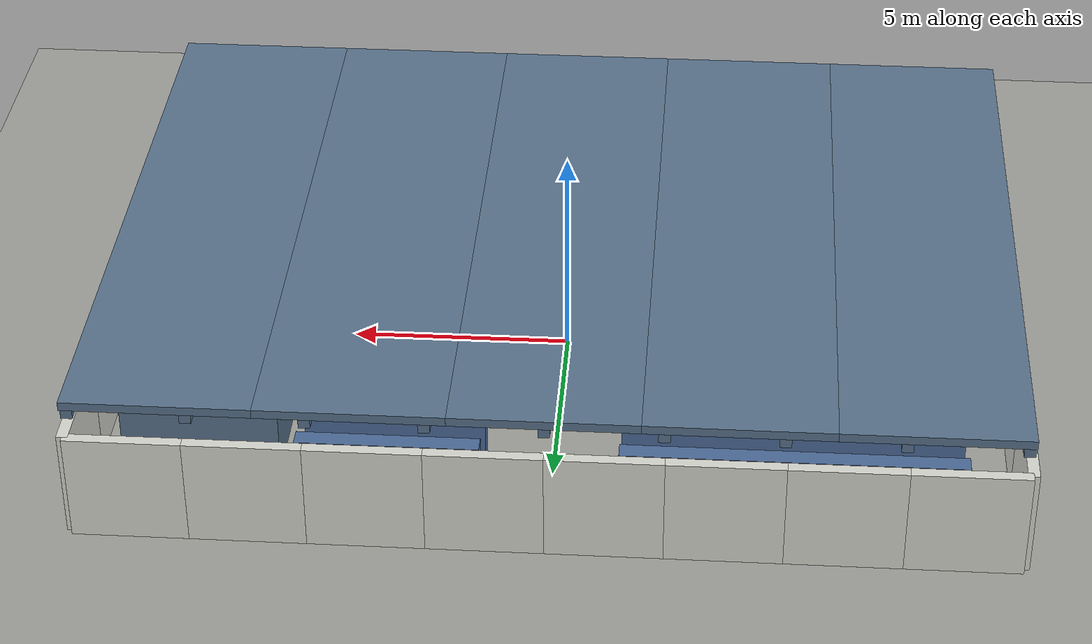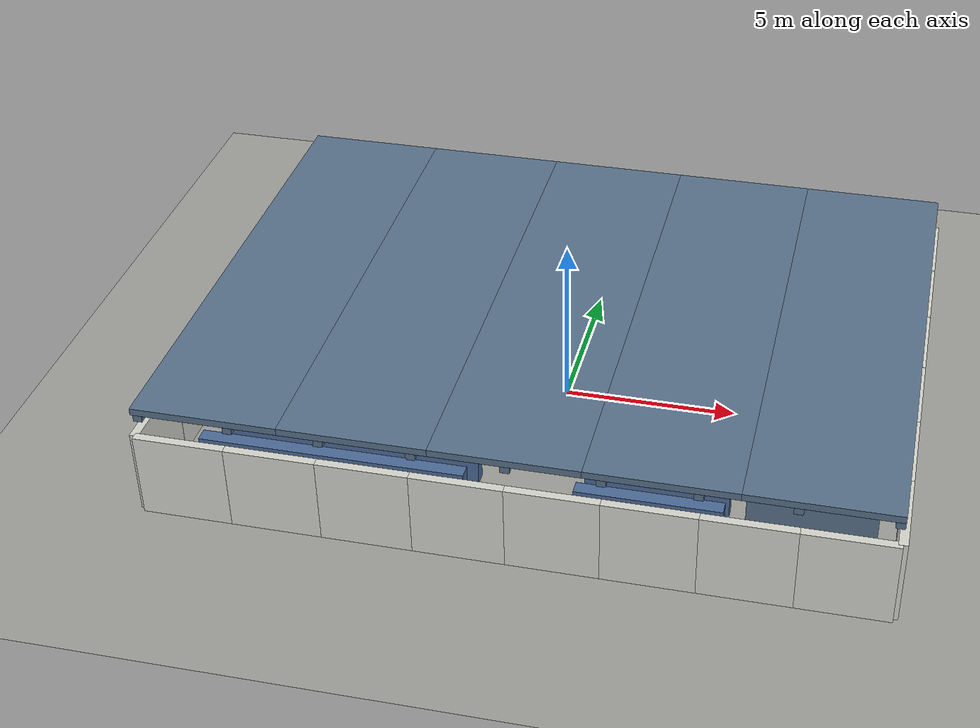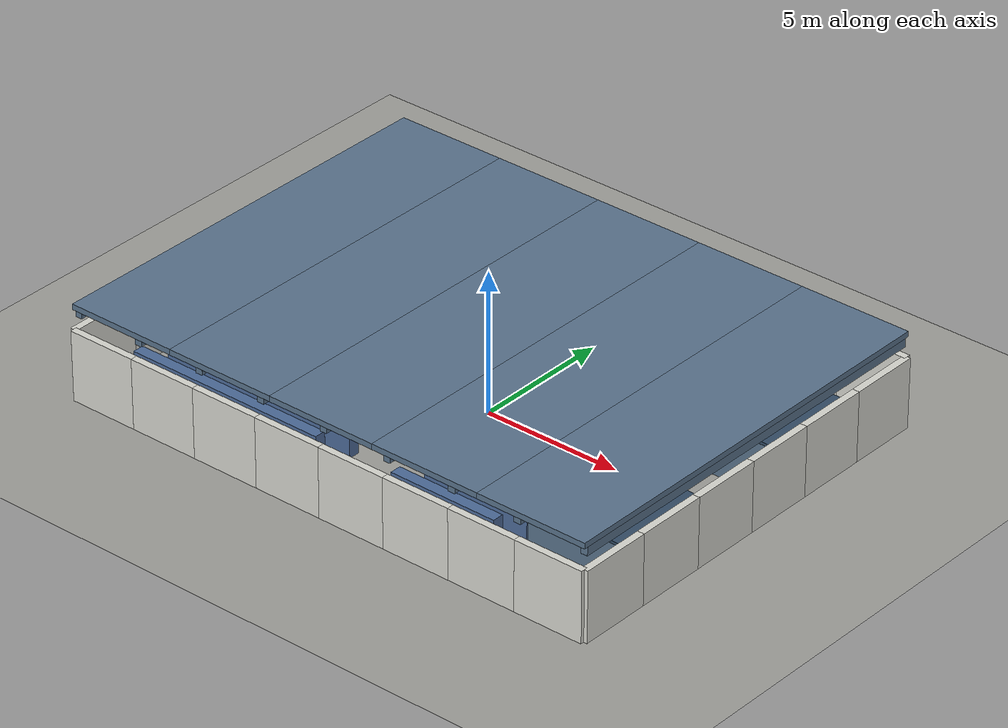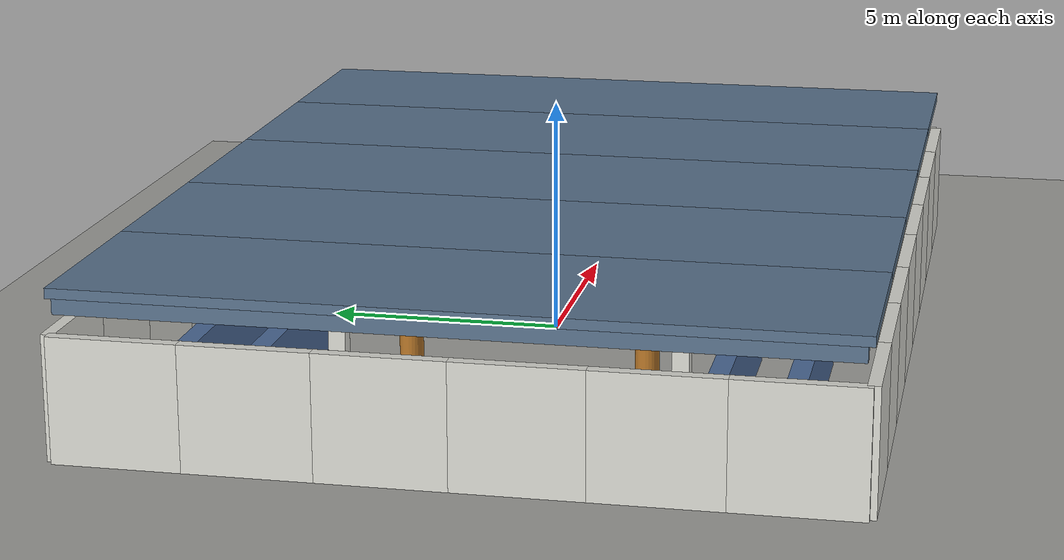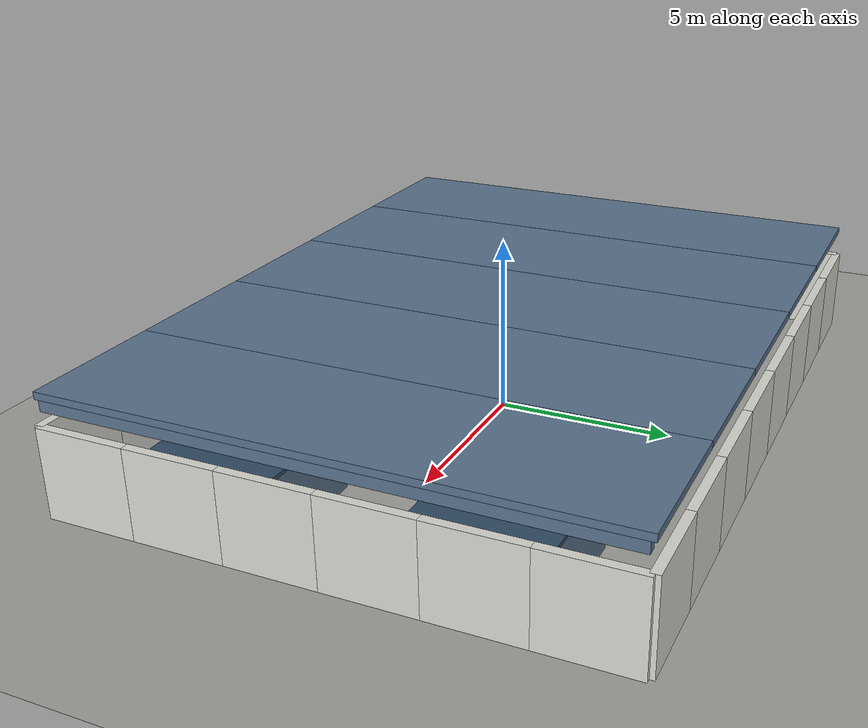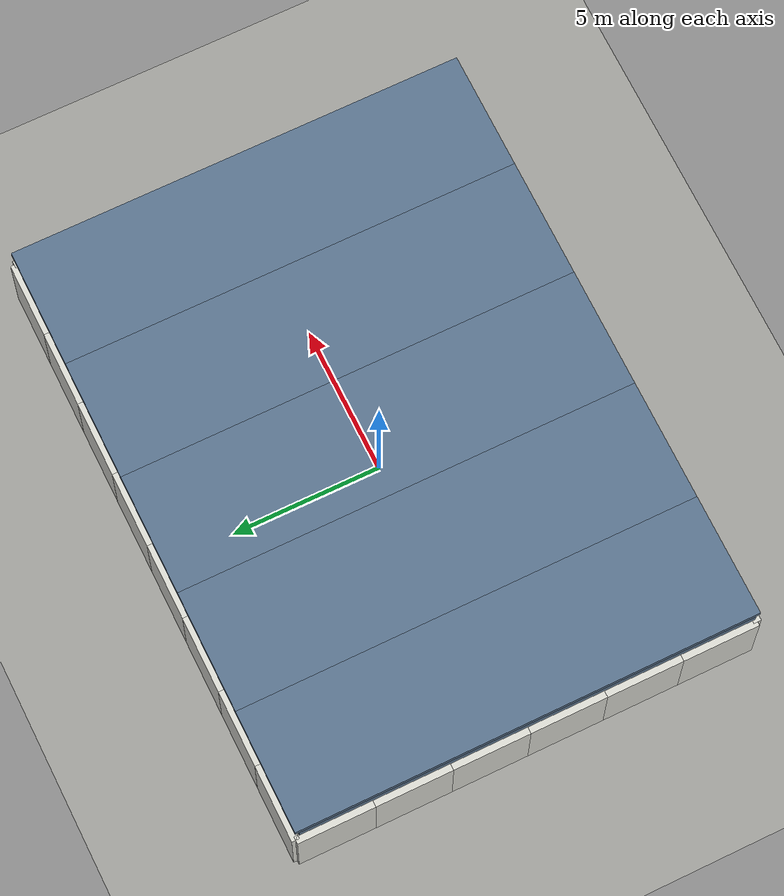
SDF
<sdf version='1.9'>
  <world name='default'>

    <gui fullscreen='0'>
      <plugin filename='MinimalScene' name='3D View'>
        <ignition-gui>
          <title>3D View</title>
          <property type='bool' key='showTitleBar'>false</property>
          <property type='string' key='state'>docked</property>
        </ignition-gui>
        <engine>ogre2</engine>
        <scene>scene</scene>
        <ambient_light>0.4 0.4 0.4</ambient_light>
        <background_color>0.8 0.8 0.8</background_color>
        <camera_pose>-9.02 -6.82 2.30 0 0.114 0.647</camera_pose>
      </plugin>

      <plugin filename='GzSceneManager' name='Scene Manager'>
        <ignition-gui>
          <property key='resizable' type='bool'>false</property>
          <property key='showTitleBar' type='bool'>false</property>
          <property key='state' type='string'>floating</property>
          <property key='width' type='double'>5</property>
          <property key='height' type='double'>5</property>
        </ignition-gui>
      </plugin>

      <plugin filename='InteractiveViewControl' name='Interactive view control'>
        <ignition-gui>
          <property key='resizable' type='bool'>false</property>
          <property key='showTitleBar' type='bool'>false</property>
          <property key='state' type='string'>floating</property>
          <property key='width' type='double'>5</property>
          <property key='height' type='double'>5</property>
        </ignition-gui>
      </plugin>

      <plugin filename='CameraTracking' name='Camera Tracking'>
        <ignition-gui>
          <property key='resizable' type='bool'>false</property>
          <property key='showTitleBar' type='bool'>false</property>
          <property key='state' type='string'>floating</property>
          <property key='width' type='double'>5</property>
          <property key='height' type='double'>5</property>
        </ignition-gui>
      </plugin>

      <plugin filename='WorldControl' name='World control'>
        <ignition-gui>
          <title>World control</title>
          <property type='bool' key='showTitleBar'>false</property>
          <property type='bool' key='resizable'>false</property>
          <property type='double' key='height'>72</property>
          <property type='double' key='z'>1</property>
          <property type='string' key='state'>floating</property>
          <anchors target='3D View'>
            <line own='left' target='left'/>
            <line own='bottom' target='bottom'/>
          </anchors>
        </ignition-gui>
        <play_pause>true</play_pause>
        <step>true</step>
        <start_paused>false</start_paused>
      </plugin>

      <plugin filename='WorldStats' name='World stats'>
        <ignition-gui>
          <title>World stats</title>
          <property type='bool' key='showTitleBar'>false</property>
          <property type='bool' key='resizable'>false</property>
          <property type='double' key='height'>110</property>
          <property type='double' key='width'>290</property>
          <property type='double' key='z'>1</property>
          <property type='string' key='state'>floating</property>
          <anchors target='3D View'>
            <line own='right' target='right'/>
            <line own='bottom' target='bottom'/>
          </anchors>
        </ignition-gui>
        <sim_time>true</sim_time>
        <real_time>true</real_time>
        <real_time_factor>true</real_time_factor>
        <iterations>true</iterations>
      </plugin>
    </gui>

    <plugin filename="gz-sim-physics-system" name="gz::sim::systems::Physics"/>
    <plugin filename="gz-sim-scene-broadcaster-system" name="gz::sim::systems::SceneBroadcaster"/>
    <plugin filename="gz-sim-user-commands-system" name="gz::sim::systems::UserCommands"/>
    <plugin filename="gz-sim-sensors-system" name="gz::sim::systems::Sensors">
      <render_engine>ogre2</render_engine>
    </plugin>
    <plugin filename="gz-sim-contact-system" name="gz::sim::systems::Contact"/>
    <plugin filename="gz-sim-imu-system" name="gz::sim::systems::Imu"/>

    <gravity>0 0 -9.8</gravity>
    <physics name='default_physics' type='ode'>
      <max_step_size>0.001</max_step_size>
      <real_time_factor>1.0</real_time_factor>
      <real_time_update_rate>1000</real_time_update_rate>
    </physics>

    <scene>
      <ambient>0.72 0.72 0.72 1</ambient>
      <background>0.7 0.72 0.75 1</background>
      <shadows>true</shadows>
    </scene>

    <light type='point' name='bay_light_0'>
      <pose>-7.5 -4.5 3.0 0 0 0</pose>
      <cast_shadows>false</cast_shadows>
      <diffuse>0.75 0.74 0.70 1</diffuse>
      <specular>0.12 0.12 0.12 1</specular>
      <attenuation>
        <range>26</range>
        <constant>0.42</constant>
        <linear>0.02</linear>
        <quadratic>0.002</quadratic>
      </attenuation>
    </light>
    <light type='point' name='bay_light_1'>
      <pose>-7.5 0.0 3.0 0 0 0</pose>
      <cast_shadows>false</cast_shadows>
      <diffuse>0.75 0.74 0.70 1</diffuse>
      <specular>0.12 0.12 0.12 1</specular>
      <attenuation>
        <range>26</range>
        <constant>0.42</constant>
        <linear>0.02</linear>
        <quadratic>0.002</quadratic>
      </attenuation>
    </light>
    <light type='point' name='bay_light_2'>
      <pose>-7.5 4.5 3.0 0 0 0</pose>
      <cast_shadows>false</cast_shadows>
      <diffuse>0.75 0.74 0.70 1</diffuse>
      <specular>0.12 0.12 0.12 1</specular>
      <attenuation>
        <range>26</range>
        <constant>0.42</constant>
        <linear>0.02</linear>
        <quadratic>0.002</quadratic>
      </attenuation>
    </light>
    <light type='point' name='bay_light_3'>
      <pose>-2.5 -4.5 3.0 0 0 0</pose>
      <cast_shadows>false</cast_shadows>
      <diffuse>0.75 0.74 0.70 1</diffuse>
      <specular>0.12 0.12 0.12 1</specular>
      <attenuation>
        <range>26</range>
        <constant>0.42</constant>
        <linear>0.02</linear>
        <quadratic>0.002</quadratic>
      </attenuation>
    </light>
    <light type='point' name='bay_light_4'>
      <pose>-2.5 0.0 3.0 0 0 0</pose>
      <cast_shadows>false</cast_shadows>
      <diffuse>0.75 0.74 0.70 1</diffuse>
      <specular>0.12 0.12 0.12 1</specular>
      <attenuation>
        <range>26</range>
        <constant>0.42</constant>
        <linear>0.02</linear>
        <quadratic>0.002</quadratic>
      </attenuation>
    </light>
    <light type='point' name='bay_light_5'>
      <pose>-2.5 4.5 3.0 0 0 0</pose>
      <cast_shadows>false</cast_shadows>
      <diffuse>0.75 0.74 0.70 1</diffuse>
      <specular>0.12 0.12 0.12 1</specular>
      <attenuation>
        <range>26</range>
        <constant>0.42</constant>
        <linear>0.02</linear>
        <quadratic>0.002</quadratic>
      </attenuation>
    </light>
    <light type='point' name='bay_light_6'>
      <pose>2.5 -4.5 3.0 0 0 0</pose>
      <cast_shadows>false</cast_shadows>
      <diffuse>0.75 0.74 0.70 1</diffuse>
      <specular>0.12 0.12 0.12 1</specular>
      <attenuation>
        <range>26</range>
        <constant>0.42</constant>
        <linear>0.02</linear>
        <quadratic>0.002</quadratic>
      </attenuation>
    </light>
    <light type='point' name='bay_light_7'>
      <pose>2.5 0.0 3.0 0 0 0</pose>
      <cast_shadows>false</cast_shadows>
      <diffuse>0.75 0.74 0.70 1</diffuse>
      <specular>0.12 0.12 0.12 1</specular>
      <attenuation>
        <range>26</range>
        <constant>0.42</constant>
        <linear>0.02</linear>
        <quadratic>0.002</quadratic>
      </attenuation>
    </light>
    <light type='point' name='bay_light_8'>
      <pose>2.5 4.5 3.0 0 0 0</pose>
      <cast_shadows>false</cast_shadows>
      <diffuse>0.75 0.74 0.70 1</diffuse>
      <specular>0.12 0.12 0.12 1</specular>
      <attenuation>
        <range>26</range>
        <constant>0.42</constant>
        <linear>0.02</linear>
        <quadratic>0.002</quadratic>
      </attenuation>
    </light>
    <light type='point' name='bay_light_9'>
      <pose>7.5 -4.5 3.0 0 0 0</pose>
      <cast_shadows>false</cast_shadows>
      <diffuse>0.75 0.74 0.70 1</diffuse>
      <specular>0.12 0.12 0.12 1</specular>
      <attenuation>
        <range>26</range>
        <constant>0.42</constant>
        <linear>0.02</linear>
        <quadratic>0.002</quadratic>
      </attenuation>
    </light>
    <light type='point' name='bay_light_10'>
      <pose>7.5 0.0 3.0 0 0 0</pose>
      <cast_shadows>false</cast_shadows>
      <diffuse>0.75 0.74 0.70 1</diffuse>
      <specular>0.12 0.12 0.12 1</specular>
      <attenuation>
        <range>26</range>
        <constant>0.42</constant>
        <linear>0.02</linear>
        <quadratic>0.002</quadratic>
      </attenuation>
    </light>
    <light type='point' name='bay_light_11'>
      <pose>7.5 4.5 3.0 0 0 0</pose>
      <cast_shadows>false</cast_shadows>
      <diffuse>0.75 0.74 0.70 1</diffuse>
      <specular>0.12 0.12 0.12 1</specular>
      <attenuation>
        <range>26</range>
        <constant>0.42</constant>
        <linear>0.02</linear>
        <quadratic>0.002</quadratic>
      </attenuation>
    </light>
    <light type='directional' name='sun'>
      <cast_shadows>true</cast_shadows>
      <pose>0 0 12 0 0 0</pose>
      <diffuse>0.9 0.9 0.9 1</diffuse>
      <specular>0.2 0.2 0.2 1</specular>
      <attenuation>
        <range>1000</range>
        <constant>0.9</constant>
        <linear>0.01</linear>
        <quadratic>0.001</quadratic>
      </attenuation>
      <direction>-0.4 0.3 -0.9</direction>
    </light>

    <model name='ground_plane'>
      <static>true</static>
      <link name='link'>
        <collision name='collision'>
          <geometry><plane><normal>0 0 1</normal><size>200 200</size></plane></geometry>
          <surface>
            <friction>
              <ode>
                <mu>1.0</mu>
                <mu2>1.0</mu2>
              </ode>
            </friction>
          </surface>
        </collision>
        <visual name='visual'>
          <geometry><plane><normal>0 0 1</normal><size>200 200</size></plane></geometry>
          <material>
            <ambient>0.310 0.310 0.300 1</ambient>
            <diffuse>0.620 0.620 0.600 1</diffuse>
            <specular>0.05 0.05 0.05 1</specular>
            <pbr>
              <metal>
                <albedo_map>materials/textures/concrete.png</albedo_map>
                <metalness>0.0</metalness>
                <roughness>0.9</roughness>
              </metal>
            </pbr>
          </material>
        </visual>
      </link>
    </model>

    <model name='wall_north_0'>
      <static>true</static>
      <pose>-8.85938 7.62500 1.25000 0 0.000000 0</pose>
      <link name='link'>
        <collision name='collision'>
          <geometry><box><size>2.53125 0.25000 2.50000</size></box></geometry>
          <surface>
            <friction>
              <ode>
                <mu>1.0</mu>
                <mu2>1.0</mu2>
              </ode>
            </friction>
          </surface>
        </collision>
        <visual name='visual'>
          <geometry><box><size>2.53125 0.25000 2.50000</size></box></geometry>
          <material>
            <ambient>0.425 0.425 0.410 1</ambient>
            <diffuse>0.850 0.850 0.820 1</diffuse>
            <specular>0.1 0.1 0.1 1</specular>
            <pbr>
              <metal>
                <albedo_map>materials/textures/painted_wall.png</albedo_map>
                <metalness>0.0</metalness>
                <roughness>0.85</roughness>
              </metal>
            </pbr>
          </material>
        </visual>
      </link>
    </model>
    <model name='wall_north_1'>
      <static>true</static>
      <pose>-6.32812 7.62500 1.25000 0 0.000000 0</pose>
      <link name='link'>
        <collision name='collision'>
          <geometry><box><size>2.53125 0.25000 2.50000</size></box></geometry>
          <surface>
            <friction>
              <ode>
                <mu>1.0</mu>
                <mu2>1.0</mu2>
              </ode>
            </friction>
          </surface>
        </collision>
        <visual name='visual'>
          <geometry><box><size>2.53125 0.25000 2.50000</size></box></geometry>
          <material>
            <ambient>0.425 0.425 0.410 1</ambient>
            <diffuse>0.850 0.850 0.820 1</diffuse>
            <specular>0.1 0.1 0.1 1</specular>
            <pbr>
              <metal>
                <albedo_map>materials/textures/painted_wall.png</albedo_map>
                <metalness>0.0</metalness>
                <roughness>0.85</roughness>
              </metal>
            </pbr>
          </material>
        </visual>
      </link>
    </model>
    <model name='wall_north_2'>
      <static>true</static>
      <pose>-3.79688 7.62500 1.25000 0 0.000000 0</pose>
      <link name='link'>
        <collision name='collision'>
          <geometry><box><size>2.53125 0.25000 2.50000</size></box></geometry>
          <surface>
            <friction>
              <ode>
                <mu>1.0</mu>
                <mu2>1.0</mu2>
              </ode>
            </friction>
          </surface>
        </collision>
        <visual name='visual'>
          <geometry><box><size>2.53125 0.25000 2.50000</size></box></geometry>
          <material>
            <ambient>0.425 0.425 0.410 1</ambient>
            <diffuse>0.850 0.850 0.820 1</diffuse>
            <specular>0.1 0.1 0.1 1</specular>
            <pbr>
              <metal>
                <albedo_map>materials/textures/painted_wall.png</albedo_map>
                <metalness>0.0</metalness>
                <roughness>0.85</roughness>
              </metal>
            </pbr>
          </material>
        </visual>
      </link>
    </model>
    <model name='wall_north_3'>
      <static>true</static>
      <pose>-1.26562 7.62500 1.25000 0 0.000000 0</pose>
      <link name='link'>
        <collision name='collision'>
          <geometry><box><size>2.53125 0.25000 2.50000</size></box></geometry>
          <surface>
            <friction>
              <ode>
                <mu>1.0</mu>
                <mu2>1.0</mu2>
              </ode>
            </friction>
          </surface>
        </collision>
        <visual name='visual'>
          <geometry><box><size>2.53125 0.25000 2.50000</size></box></geometry>
          <material>
            <ambient>0.425 0.425 0.410 1</ambient>
            <diffuse>0.850 0.850 0.820 1</diffuse>
            <specular>0.1 0.1 0.1 1</specular>
            <pbr>
              <metal>
                <albedo_map>materials/textures/painted_wall.png</albedo_map>
                <metalness>0.0</metalness>
                <roughness>0.85</roughness>
              </metal>
            </pbr>
          </material>
        </visual>
      </link>
    </model>
    <model name='wall_north_4'>
      <static>true</static>
      <pose>1.26562 7.62500 1.25000 0 0.000000 0</pose>
      <link name='link'>
        <collision name='collision'>
          <geometry><box><size>2.53125 0.25000 2.50000</size></box></geometry>
          <surface>
            <friction>
              <ode>
                <mu>1.0</mu>
                <mu2>1.0</mu2>
              </ode>
            </friction>
          </surface>
        </collision>
        <visual name='visual'>
          <geometry><box><size>2.53125 0.25000 2.50000</size></box></geometry>
          <material>
            <ambient>0.425 0.425 0.410 1</ambient>
            <diffuse>0.850 0.850 0.820 1</diffuse>
            <specular>0.1 0.1 0.1 1</specular>
            <pbr>
              <metal>
                <albedo_map>materials/textures/painted_wall.png</albedo_map>
                <metalness>0.0</metalness>
                <roughness>0.85</roughness>
              </metal>
            </pbr>
          </material>
        </visual>
      </link>
    </model>
    <model name='wall_north_5'>
      <static>true</static>
      <pose>3.79688 7.62500 1.25000 0 0.000000 0</pose>
      <link name='link'>
        <collision name='collision'>
          <geometry><box><size>2.53125 0.25000 2.50000</size></box></geometry>
          <surface>
            <friction>
              <ode>
                <mu>1.0</mu>
                <mu2>1.0</mu2>
              </ode>
            </friction>
          </surface>
        </collision>
        <visual name='visual'>
          <geometry><box><size>2.53125 0.25000 2.50000</size></box></geometry>
          <material>
            <ambient>0.425 0.425 0.410 1</ambient>
            <diffuse>0.850 0.850 0.820 1</diffuse>
            <specular>0.1 0.1 0.1 1</specular>
            <pbr>
              <metal>
                <albedo_map>materials/textures/painted_wall.png</albedo_map>
                <metalness>0.0</metalness>
                <roughness>0.85</roughness>
              </metal>
            </pbr>
          </material>
        </visual>
      </link>
    </model>
    <model name='wall_north_6'>
      <static>true</static>
      <pose>6.32812 7.62500 1.25000 0 0.000000 0</pose>
      <link name='link'>
        <collision name='collision'>
          <geometry><box><size>2.53125 0.25000 2.50000</size></box></geometry>
          <surface>
            <friction>
              <ode>
                <mu>1.0</mu>
                <mu2>1.0</mu2>
              </ode>
            </friction>
          </surface>
        </collision>
        <visual name='visual'>
          <geometry><box><size>2.53125 0.25000 2.50000</size></box></geometry>
          <material>
            <ambient>0.425 0.425 0.410 1</ambient>
            <diffuse>0.850 0.850 0.820 1</diffuse>
            <specular>0.1 0.1 0.1 1</specular>
            <pbr>
              <metal>
                <albedo_map>materials/textures/painted_wall.png</albedo_map>
                <metalness>0.0</metalness>
                <roughness>0.85</roughness>
              </metal>
            </pbr>
          </material>
        </visual>
      </link>
    </model>
    <model name='wall_north_7'>
      <static>true</static>
      <pose>8.85938 7.62500 1.25000 0 0.000000 0</pose>
      <link name='link'>
        <collision name='collision'>
          <geometry><box><size>2.53125 0.25000 2.50000</size></box></geometry>
          <surface>
            <friction>
              <ode>
                <mu>1.0</mu>
                <mu2>1.0</mu2>
              </ode>
            </friction>
          </surface>
        </collision>
        <visual name='visual'>
          <geometry><box><size>2.53125 0.25000 2.50000</size></box></geometry>
          <material>
            <ambient>0.425 0.425 0.410 1</ambient>
            <diffuse>0.850 0.850 0.820 1</diffuse>
            <specular>0.1 0.1 0.1 1</specular>
            <pbr>
              <metal>
                <albedo_map>materials/textures/painted_wall.png</albedo_map>
                <metalness>0.0</metalness>
                <roughness>0.85</roughness>
              </metal>
            </pbr>
          </material>
        </visual>
      </link>
    </model>
    <model name='wall_south_0'>
      <static>true</static>
      <pose>-8.85938 -7.62500 1.25000 0 0.000000 0</pose>
      <link name='link'>
        <collision name='collision'>
          <geometry><box><size>2.53125 0.25000 2.50000</size></box></geometry>
          <surface>
            <friction>
              <ode>
                <mu>1.0</mu>
                <mu2>1.0</mu2>
              </ode>
            </friction>
          </surface>
        </collision>
        <visual name='visual'>
          <geometry><box><size>2.53125 0.25000 2.50000</size></box></geometry>
          <material>
            <ambient>0.425 0.425 0.410 1</ambient>
            <diffuse>0.850 0.850 0.820 1</diffuse>
            <specular>0.1 0.1 0.1 1</specular>
            <pbr>
              <metal>
                <albedo_map>materials/textures/painted_wall.png</albedo_map>
                <metalness>0.0</metalness>
                <roughness>0.85</roughness>
              </metal>
            </pbr>
          </material>
        </visual>
      </link>
    </model>
    <model name='wall_south_1'>
      <static>true</static>
      <pose>-6.32812 -7.62500 1.25000 0 0.000000 0</pose>
      <link name='link'>
        <collision name='collision'>
          <geometry><box><size>2.53125 0.25000 2.50000</size></box></geometry>
          <surface>
            <friction>
              <ode>
                <mu>1.0</mu>
                <mu2>1.0</mu2>
              </ode>
            </friction>
          </surface>
        </collision>
        <visual name='visual'>
          <geometry><box><size>2.53125 0.25000 2.50000</size></box></geometry>
          <material>
            <ambient>0.425 0.425 0.410 1</ambient>
            <diffuse>0.850 0.850 0.820 1</diffuse>
            <specular>0.1 0.1 0.1 1</specular>
            <pbr>
              <metal>
                <albedo_map>materials/textures/painted_wall.png</albedo_map>
                <metalness>0.0</metalness>
                <roughness>0.85</roughness>
              </metal>
            </pbr>
          </material>
        </visual>
      </link>
    </model>
    <model name='wall_south_2'>
      <static>true</static>
      <pose>-3.79688 -7.62500 1.25000 0 0.000000 0</pose>
      <link name='link'>
        <collision name='collision'>
          <geometry><box><size>2.53125 0.25000 2.50000</size></box></geometry>
          <surface>
            <friction>
              <ode>
                <mu>1.0</mu>
                <mu2>1.0</mu2>
              </ode>
            </friction>
          </surface>
        </collision>
        <visual name='visual'>
          <geometry><box><size>2.53125 0.25000 2.50000</size></box></geometry>
          <material>
            <ambient>0.425 0.425 0.410 1</ambient>
            <diffuse>0.850 0.850 0.820 1</diffuse>
            <specular>0.1 0.1 0.1 1</specular>
            <pbr>
              <metal>
                <albedo_map>materials/textures/painted_wall.png</albedo_map>
                <metalness>0.0</metalness>
                <roughness>0.85</roughness>
              </metal>
            </pbr>
          </material>
        </visual>
      </link>
    </model>
    <model name='wall_south_3'>
      <static>true</static>
      <pose>-1.26562 -7.62500 1.25000 0 0.000000 0</pose>
      <link name='link'>
        <collision name='collision'>
          <geometry><box><size>2.53125 0.25000 2.50000</size></box></geometry>
          <surface>
            <friction>
              <ode>
                <mu>1.0</mu>
                <mu2>1.0</mu2>
              </ode>
            </friction>
          </surface>
        </collision>
        <visual name='visual'>
          <geometry><box><size>2.53125 0.25000 2.50000</size></box></geometry>
          <material>
            <ambient>0.425 0.425 0.410 1</ambient>
            <diffuse>0.850 0.850 0.820 1</diffuse>
            <specular>0.1 0.1 0.1 1</specular>
            <pbr>
              <metal>
                <albedo_map>materials/textures/painted_wall.png</albedo_map>
                <metalness>0.0</metalness>
                <roughness>0.85</roughness>
              </metal>
            </pbr>
          </material>
        </visual>
      </link>
    </model>
    <model name='wall_south_4'>
      <static>true</static>
      <pose>1.26562 -7.62500 1.25000 0 0.000000 0</pose>
      <link name='link'>
        <collision name='collision'>
          <geometry><box><size>2.53125 0.25000 2.50000</size></box></geometry>
          <surface>
            <friction>
              <ode>
                <mu>1.0</mu>
                <mu2>1.0</mu2>
              </ode>
            </friction>
          </surface>
        </collision>
        <visual name='visual'>
          <geometry><box><size>2.53125 0.25000 2.50000</size></box></geometry>
          <material>
            <ambient>0.425 0.425 0.410 1</ambient>
            <diffuse>0.850 0.850 0.820 1</diffuse>
            <specular>0.1 0.1 0.1 1</specular>
            <pbr>
              <metal>
                <albedo_map>materials/textures/painted_wall.png</albedo_map>
                <metalness>0.0</metalness>
                <roughness>0.85</roughness>
              </metal>
            </pbr>
          </material>
        </visual>
      </link>
    </model>
    <model name='wall_south_5'>
      <static>true</static>
      <pose>3.79688 -7.62500 1.25000 0 0.000000 0</pose>
      <link name='link'>
        <collision name='collision'>
          <geometry><box><size>2.53125 0.25000 2.50000</size></box></geometry>
          <surface>
            <friction>
              <ode>
                <mu>1.0</mu>
                <mu2>1.0</mu2>
              </ode>
            </friction>
          </surface>
        </collision>
        <visual name='visual'>
          <geometry><box><size>2.53125 0.25000 2.50000</size></box></geometry>
          <material>
            <ambient>0.425 0.425 0.410 1</ambient>
            <diffuse>0.850 0.850 0.820 1</diffuse>
            <specular>0.1 0.1 0.1 1</specular>
            <pbr>
              <metal>
                <albedo_map>materials/textures/painted_wall.png</albedo_map>
                <metalness>0.0</metalness>
                <roughness>0.85</roughness>
              </metal>
            </pbr>
          </material>
        </visual>
      </link>
    </model>
    <model name='wall_south_6'>
      <static>true</static>
      <pose>6.32812 -7.62500 1.25000 0 0.000000 0</pose>
      <link name='link'>
        <collision name='collision'>
          <geometry><box><size>2.53125 0.25000 2.50000</size></box></geometry>
          <surface>
            <friction>
              <ode>
                <mu>1.0</mu>
                <mu2>1.0</mu2>
              </ode>
            </friction>
          </surface>
        </collision>
        <visual name='visual'>
          <geometry><box><size>2.53125 0.25000 2.50000</size></box></geometry>
          <material>
            <ambient>0.425 0.425 0.410 1</ambient>
            <diffuse>0.850 0.850 0.820 1</diffuse>
            <specular>0.1 0.1 0.1 1</specular>
            <pbr>
              <metal>
                <albedo_map>materials/textures/painted_wall.png</albedo_map>
                <metalness>0.0</metalness>
                <roughness>0.85</roughness>
              </metal>
            </pbr>
          </material>
        </visual>
      </link>
    </model>
    <model name='wall_south_7'>
      <static>true</static>
      <pose>8.85938 -7.62500 1.25000 0 0.000000 0</pose>
      <link name='link'>
        <collision name='collision'>
          <geometry><box><size>2.53125 0.25000 2.50000</size></box></geometry>
          <surface>
            <friction>
              <ode>
                <mu>1.0</mu>
                <mu2>1.0</mu2>
              </ode>
            </friction>
          </surface>
        </collision>
        <visual name='visual'>
          <geometry><box><size>2.53125 0.25000 2.50000</size></box></geometry>
          <material>
            <ambient>0.425 0.425 0.410 1</ambient>
            <diffuse>0.850 0.850 0.820 1</diffuse>
            <specular>0.1 0.1 0.1 1</specular>
            <pbr>
              <metal>
                <albedo_map>materials/textures/painted_wall.png</albedo_map>
                <metalness>0.0</metalness>
                <roughness>0.85</roughness>
              </metal>
            </pbr>
          </material>
        </visual>
      </link>
    </model>
    <model name='wall_east_0'>
      <static>true</static>
      <pose>10.12500 -6.35417 1.25000 0 0.000000 0</pose>
      <link name='link'>
        <collision name='collision'>
          <geometry><box><size>0.25000 2.54167 2.50000</size></box></geometry>
          <surface>
            <friction>
              <ode>
                <mu>1.0</mu>
                <mu2>1.0</mu2>
              </ode>
            </friction>
          </surface>
        </collision>
        <visual name='visual'>
          <geometry><box><size>0.25000 2.54167 2.50000</size></box></geometry>
          <material>
            <ambient>0.425 0.425 0.410 1</ambient>
            <diffuse>0.850 0.850 0.820 1</diffuse>
            <specular>0.1 0.1 0.1 1</specular>
            <pbr>
              <metal>
                <albedo_map>materials/textures/painted_wall.png</albedo_map>
                <metalness>0.0</metalness>
                <roughness>0.85</roughness>
              </metal>
            </pbr>
          </material>
        </visual>
      </link>
    </model>
    <model name='wall_east_1'>
      <static>true</static>
      <pose>10.12500 -3.81250 1.25000 0 0.000000 0</pose>
      <link name='link'>
        <collision name='collision'>
          <geometry><box><size>0.25000 2.54167 2.50000</size></box></geometry>
          <surface>
            <friction>
              <ode>
                <mu>1.0</mu>
                <mu2>1.0</mu2>
              </ode>
            </friction>
          </surface>
        </collision>
        <visual name='visual'>
          <geometry><box><size>0.25000 2.54167 2.50000</size></box></geometry>
          <material>
            <ambient>0.425 0.425 0.410 1</ambient>
            <diffuse>0.850 0.850 0.820 1</diffuse>
            <specular>0.1 0.1 0.1 1</specular>
            <pbr>
              <metal>
                <albedo_map>materials/textures/painted_wall.png</albedo_map>
                <metalness>0.0</metalness>
                <roughness>0.85</roughness>
              </metal>
            </pbr>
          </material>
        </visual>
      </link>
    </model>
    <model name='wall_east_2'>
      <static>true</static>
      <pose>10.12500 -1.27083 1.25000 0 0.000000 0</pose>
      <link name='link'>
        <collision name='collision'>
          <geometry><box><size>0.25000 2.54167 2.50000</size></box></geometry>
          <surface>
            <friction>
              <ode>
                <mu>1.0</mu>
                <mu2>1.0</mu2>
              </ode>
            </friction>
          </surface>
        </collision>
        <visual name='visual'>
          <geometry><box><size>0.25000 2.54167 2.50000</size></box></geometry>
          <material>
            <ambient>0.425 0.425 0.410 1</ambient>
            <diffuse>0.850 0.850 0.820 1</diffuse>
            <specular>0.1 0.1 0.1 1</specular>
            <pbr>
              <metal>
                <albedo_map>materials/textures/painted_wall.png</albedo_map>
                <metalness>0.0</metalness>
                <roughness>0.85</roughness>
              </metal>
            </pbr>
          </material>
        </visual>
      </link>
    </model>
    <model name='wall_east_3'>
      <static>true</static>
      <pose>10.12500 1.27083 1.25000 0 0.000000 0</pose>
      <link name='link'>
        <collision name='collision'>
          <geometry><box><size>0.25000 2.54167 2.50000</size></box></geometry>
          <surface>
            <friction>
              <ode>
                <mu>1.0</mu>
                <mu2>1.0</mu2>
              </ode>
            </friction>
          </surface>
        </collision>
        <visual name='visual'>
          <geometry><box><size>0.25000 2.54167 2.50000</size></box></geometry>
          <material>
            <ambient>0.425 0.425 0.410 1</ambient>
            <diffuse>0.850 0.850 0.820 1</diffuse>
            <specular>0.1 0.1 0.1 1</specular>
            <pbr>
              <metal>
                <albedo_map>materials/textures/painted_wall.png</albedo_map>
                <metalness>0.0</metalness>
                <roughness>0.85</roughness>
              </metal>
            </pbr>
          </material>
        </visual>
      </link>
    </model>
    <model name='wall_east_4'>
      <static>true</static>
      <pose>10.12500 3.81250 1.25000 0 0.000000 0</pose>
      <link name='link'>
        <collision name='collision'>
          <geometry><box><size>0.25000 2.54167 2.50000</size></box></geometry>
          <surface>
            <friction>
              <ode>
                <mu>1.0</mu>
                <mu2>1.0</mu2>
              </ode>
            </friction>
          </surface>
        </collision>
        <visual name='visual'>
          <geometry><box><size>0.25000 2.54167 2.50000</size></box></geometry>
          <material>
            <ambient>0.425 0.425 0.410 1</ambient>
            <diffuse>0.850 0.850 0.820 1</diffuse>
            <specular>0.1 0.1 0.1 1</specular>
            <pbr>
              <metal>
                <albedo_map>materials/textures/painted_wall.png</albedo_map>
                <metalness>0.0</metalness>
                <roughness>0.85</roughness>
              </metal>
            </pbr>
          </material>
        </visual>
      </link>
    </model>
    <model name='wall_east_5'>
      <static>true</static>
      <pose>10.12500 6.35417 1.25000 0 0.000000 0</pose>
      <link name='link'>
        <collision name='collision'>
          <geometry><box><size>0.25000 2.54167 2.50000</size></box></geometry>
          <surface>
            <friction>
              <ode>
                <mu>1.0</mu>
                <mu2>1.0</mu2>
              </ode>
            </friction>
          </surface>
        </collision>
        <visual name='visual'>
          <geometry><box><size>0.25000 2.54167 2.50000</size></box></geometry>
          <material>
            <ambient>0.425 0.425 0.410 1</ambient>
            <diffuse>0.850 0.850 0.820 1</diffuse>
            <specular>0.1 0.1 0.1 1</specular>
            <pbr>
              <metal>
                <albedo_map>materials/textures/painted_wall.png</albedo_map>
                <metalness>0.0</metalness>
                <roughness>0.85</roughness>
              </metal>
            </pbr>
          </material>
        </visual>
      </link>
    </model>
    <model name='wall_west_0'>
      <static>true</static>
      <pose>-10.12500 -6.35417 1.25000 0 0.000000 0</pose>
      <link name='link'>
        <collision name='collision'>
          <geometry><box><size>0.25000 2.54167 2.50000</size></box></geometry>
          <surface>
            <friction>
              <ode>
                <mu>1.0</mu>
                <mu2>1.0</mu2>
              </ode>
            </friction>
          </surface>
        </collision>
        <visual name='visual'>
          <geometry><box><size>0.25000 2.54167 2.50000</size></box></geometry>
          <material>
            <ambient>0.425 0.425 0.410 1</ambient>
            <diffuse>0.850 0.850 0.820 1</diffuse>
            <specular>0.1 0.1 0.1 1</specular>
            <pbr>
              <metal>
                <albedo_map>materials/textures/painted_wall.png</albedo_map>
                <metalness>0.0</metalness>
                <roughness>0.85</roughness>
              </metal>
            </pbr>
          </material>
        </visual>
      </link>
    </model>
    <model name='wall_west_1'>
      <static>true</static>
      <pose>-10.12500 -3.81250 1.25000 0 0.000000 0</pose>
      <link name='link'>
        <collision name='collision'>
          <geometry><box><size>0.25000 2.54167 2.50000</size></box></geometry>
          <surface>
            <friction>
              <ode>
                <mu>1.0</mu>
                <mu2>1.0</mu2>
              </ode>
            </friction>
          </surface>
        </collision>
        <visual name='visual'>
          <geometry><box><size>0.25000 2.54167 2.50000</size></box></geometry>
          <material>
            <ambient>0.425 0.425 0.410 1</ambient>
            <diffuse>0.850 0.850 0.820 1</diffuse>
            <specular>0.1 0.1 0.1 1</specular>
            <pbr>
              <metal>
                <albedo_map>materials/textures/painted_wall.png</albedo_map>
                <metalness>0.0</metalness>
                <roughness>0.85</roughness>
              </metal>
            </pbr>
          </material>
        </visual>
      </link>
    </model>
    <model name='wall_west_2'>
      <static>true</static>
      <pose>-10.12500 -1.27083 1.25000 0 0.000000 0</pose>
      <link name='link'>
        <collision name='collision'>
          <geometry><box><size>0.25000 2.54167 2.50000</size></box></geometry>
          <surface>
            <friction>
              <ode>
                <mu>1.0</mu>
                <mu2>1.0</mu2>
              </ode>
            </friction>
          </surface>
        </collision>
        <visual name='visual'>
          <geometry><box><size>0.25000 2.54167 2.50000</size></box></geometry>
          <material>
            <ambient>0.425 0.425 0.410 1</ambient>
            <diffuse>0.850 0.850 0.820 1</diffuse>
            <specular>0.1 0.1 0.1 1</specular>
            <pbr>
              <metal>
                <albedo_map>materials/textures/painted_wall.png</albedo_map>
                <metalness>0.0</metalness>
                <roughness>0.85</roughness>
              </metal>
            </pbr>
          </material>
        </visual>
      </link>
    </model>
    <model name='wall_west_3'>
      <static>true</static>
      <pose>-10.12500 1.27083 1.25000 0 0.000000 0</pose>
      <link name='link'>
        <collision name='collision'>
          <geometry><box><size>0.25000 2.54167 2.50000</size></box></geometry>
          <surface>
            <friction>
              <ode>
                <mu>1.0</mu>
                <mu2>1.0</mu2>
              </ode>
            </friction>
          </surface>
        </collision>
        <visual name='visual'>
          <geometry><box><size>0.25000 2.54167 2.50000</size></box></geometry>
          <material>
            <ambient>0.425 0.425 0.410 1</ambient>
            <diffuse>0.850 0.850 0.820 1</diffuse>
            <specular>0.1 0.1 0.1 1</specular>
            <pbr>
              <metal>
                <albedo_map>materials/textures/painted_wall.png</albedo_map>
                <metalness>0.0</metalness>
                <roughness>0.85</roughness>
              </metal>
            </pbr>
          </material>
        </visual>
      </link>
    </model>
    <model name='wall_west_4'>
      <static>true</static>
      <pose>-10.12500 3.81250 1.25000 0 0.000000 0</pose>
      <link name='link'>
        <collision name='collision'>
          <geometry><box><size>0.25000 2.54167 2.50000</size></box></geometry>
          <surface>
            <friction>
              <ode>
                <mu>1.0</mu>
                <mu2>1.0</mu2>
              </ode>
            </friction>
          </surface>
        </collision>
        <visual name='visual'>
          <geometry><box><size>0.25000 2.54167 2.50000</size></box></geometry>
          <material>
            <ambient>0.425 0.425 0.410 1</ambient>
            <diffuse>0.850 0.850 0.820 1</diffuse>
            <specular>0.1 0.1 0.1 1</specular>
            <pbr>
              <metal>
                <albedo_map>materials/textures/painted_wall.png</albedo_map>
                <metalness>0.0</metalness>
                <roughness>0.85</roughness>
              </metal>
            </pbr>
          </material>
        </visual>
      </link>
    </model>
    <model name='wall_west_5'>
      <static>true</static>
      <pose>-10.12500 6.35417 1.25000 0 0.000000 0</pose>
      <link name='link'>
        <collision name='collision'>
          <geometry><box><size>0.25000 2.54167 2.50000</size></box></geometry>
          <surface>
            <friction>
              <ode>
                <mu>1.0</mu>
                <mu2>1.0</mu2>
              </ode>
            </friction>
          </surface>
        </collision>
        <visual name='visual'>
          <geometry><box><size>0.25000 2.54167 2.50000</size></box></geometry>
          <material>
            <ambient>0.425 0.425 0.410 1</ambient>
            <diffuse>0.850 0.850 0.820 1</diffuse>
            <specular>0.1 0.1 0.1 1</specular>
            <pbr>
              <metal>
                <albedo_map>materials/textures/painted_wall.png</albedo_map>
                <metalness>0.0</metalness>
                <roughness>0.85</roughness>
              </metal>
            </pbr>
          </material>
        </visual>
      </link>
    </model>
    <model name='rack_n1a'>
      <static>true</static>
      <pose>-5.25000 4.50000 0.75000 0 0.000000 0</pose>
      <link name='link'>
        <collision name='collision'>
          <geometry><box><size>7.50000 0.40000 1.50000</size></box></geometry>
          <surface>
            <friction>
              <ode>
                <mu>1.0</mu>
                <mu2>1.0</mu2>
              </ode>
            </friction>
          </surface>
        </collision>
        <visual name='visual'>
          <geometry><box><size>7.50000 0.40000 1.50000</size></box></geometry>
          <material>
            <ambient>0.150 0.210 0.300 1</ambient>
            <diffuse>0.300 0.420 0.600 1</diffuse>
            <specular>0.1 0.1 0.1 1</specular>
            <pbr>
              <metal>
                <albedo_map>materials/textures/steel.png</albedo_map>
                <metalness>0.0</metalness>
                <roughness>0.85</roughness>
              </metal>
            </pbr>
          </material>
        </visual>
      </link>
    </model>
    <model name='rack_n1b'>
      <static>true</static>
      <pose>3.50000 4.50000 0.75000 0 0.000000 0</pose>
      <link name='link'>
        <collision name='collision'>
          <geometry><box><size>4.00000 0.40000 1.50000</size></box></geometry>
          <surface>
            <friction>
              <ode>
                <mu>1.0</mu>
                <mu2>1.0</mu2>
              </ode>
            </friction>
          </surface>
        </collision>
        <visual name='visual'>
          <geometry><box><size>4.00000 0.40000 1.50000</size></box></geometry>
          <material>
            <ambient>0.150 0.210 0.300 1</ambient>
            <diffuse>0.300 0.420 0.600 1</diffuse>
            <specular>0.1 0.1 0.1 1</specular>
            <pbr>
              <metal>
                <albedo_map>materials/textures/steel.png</albedo_map>
                <metalness>0.0</metalness>
                <roughness>0.85</roughness>
              </metal>
            </pbr>
          </material>
        </visual>
      </link>
    </model>
    <model name='rack_n2a'>
      <static>true</static>
      <pose>-5.25000 6.00000 0.75000 0 0.000000 0</pose>
      <link name='link'>
        <collision name='collision'>
          <geometry><box><size>7.50000 0.40000 1.50000</size></box></geometry>
          <surface>
            <friction>
              <ode>
                <mu>1.0</mu>
                <mu2>1.0</mu2>
              </ode>
            </friction>
          </surface>
        </collision>
        <visual name='visual'>
          <geometry><box><size>7.50000 0.40000 1.50000</size></box></geometry>
          <material>
            <ambient>0.150 0.210 0.300 1</ambient>
            <diffuse>0.300 0.420 0.600 1</diffuse>
            <specular>0.1 0.1 0.1 1</specular>
            <pbr>
              <metal>
                <albedo_map>materials/textures/steel.png</albedo_map>
                <metalness>0.0</metalness>
                <roughness>0.85</roughness>
              </metal>
            </pbr>
          </material>
        </visual>
      </link>
    </model>
    <model name='rack_n2b'>
      <static>true</static>
      <pose>3.50000 6.00000 0.75000 0 0.000000 0</pose>
      <link name='link'>
        <collision name='collision'>
          <geometry><box><size>4.00000 0.40000 1.50000</size></box></geometry>
          <surface>
            <friction>
              <ode>
                <mu>1.0</mu>
                <mu2>1.0</mu2>
              </ode>
            </friction>
          </surface>
        </collision>
        <visual name='visual'>
          <geometry><box><size>4.00000 0.40000 1.50000</size></box></geometry>
          <material>
            <ambient>0.150 0.210 0.300 1</ambient>
            <diffuse>0.300 0.420 0.600 1</diffuse>
            <specular>0.1 0.1 0.1 1</specular>
            <pbr>
              <metal>
                <albedo_map>materials/textures/steel.png</albedo_map>
                <metalness>0.0</metalness>
                <roughness>0.85</roughness>
              </metal>
            </pbr>
          </material>
        </visual>
      </link>
    </model>
    <model name='rack_s1a'>
      <static>true</static>
      <pose>-5.25000 -4.50000 0.75000 0 0.000000 0</pose>
      <link name='link'>
        <collision name='collision'>
          <geometry><box><size>7.50000 0.40000 1.50000</size></box></geometry>
          <surface>
            <friction>
              <ode>
                <mu>1.0</mu>
                <mu2>1.0</mu2>
              </ode>
            </friction>
          </surface>
        </collision>
        <visual name='visual'>
          <geometry><box><size>7.50000 0.40000 1.50000</size></box></geometry>
          <material>
            <ambient>0.150 0.210 0.300 1</ambient>
            <diffuse>0.300 0.420 0.600 1</diffuse>
            <specular>0.1 0.1 0.1 1</specular>
            <pbr>
              <metal>
                <albedo_map>materials/textures/steel.png</albedo_map>
                <metalness>0.0</metalness>
                <roughness>0.85</roughness>
              </metal>
            </pbr>
          </material>
        </visual>
      </link>
    </model>
    <model name='rack_s1b'>
      <static>true</static>
      <pose>3.50000 -4.50000 0.75000 0 0.000000 0</pose>
      <link name='link'>
        <collision name='collision'>
          <geometry><box><size>4.00000 0.40000 1.50000</size></box></geometry>
          <surface>
            <friction>
              <ode>
                <mu>1.0</mu>
                <mu2>1.0</mu2>
              </ode>
            </friction>
          </surface>
        </collision>
        <visual name='visual'>
          <geometry><box><size>4.00000 0.40000 1.50000</size></box></geometry>
          <material>
            <ambient>0.150 0.210 0.300 1</ambient>
            <diffuse>0.300 0.420 0.600 1</diffuse>
            <specular>0.1 0.1 0.1 1</specular>
            <pbr>
              <metal>
                <albedo_map>materials/textures/steel.png</albedo_map>
                <metalness>0.0</metalness>
                <roughness>0.85</roughness>
              </metal>
            </pbr>
          </material>
        </visual>
      </link>
    </model>
    <model name='rack_s2a'>
      <static>true</static>
      <pose>-5.25000 -6.00000 0.75000 0 0.000000 0</pose>
      <link name='link'>
        <collision name='collision'>
          <geometry><box><size>7.50000 0.40000 1.50000</size></box></geometry>
          <surface>
            <friction>
              <ode>
                <mu>1.0</mu>
                <mu2>1.0</mu2>
              </ode>
            </friction>
          </surface>
        </collision>
        <visual name='visual'>
          <geometry><box><size>7.50000 0.40000 1.50000</size></box></geometry>
          <material>
            <ambient>0.150 0.210 0.300 1</ambient>
            <diffuse>0.300 0.420 0.600 1</diffuse>
            <specular>0.1 0.1 0.1 1</specular>
            <pbr>
              <metal>
                <albedo_map>materials/textures/steel.png</albedo_map>
                <metalness>0.0</metalness>
                <roughness>0.85</roughness>
              </metal>
            </pbr>
          </material>
        </visual>
      </link>
    </model>
    <model name='rack_s2b'>
      <static>true</static>
      <pose>3.50000 -6.00000 0.75000 0 0.000000 0</pose>
      <link name='link'>
        <collision name='collision'>
          <geometry><box><size>4.00000 0.40000 1.50000</size></box></geometry>
          <surface>
            <friction>
              <ode>
                <mu>1.0</mu>
                <mu2>1.0</mu2>
              </ode>
            </friction>
          </surface>
        </collision>
        <visual name='visual'>
          <geometry><box><size>4.00000 0.40000 1.50000</size></box></geometry>
          <material>
            <ambient>0.150 0.210 0.300 1</ambient>
            <diffuse>0.300 0.420 0.600 1</diffuse>
            <specular>0.1 0.1 0.1 1</specular>
            <pbr>
              <metal>
                <albedo_map>materials/textures/steel.png</albedo_map>
                <metalness>0.0</metalness>
                <roughness>0.85</roughness>
              </metal>
            </pbr>
          </material>
        </visual>
      </link>
    </model>
    <model name='machine_ne'>
      <static>true</static>
      <pose>7.75000 3.50000 0.90000 0 0.000000 0</pose>
      <link name='link'>
        <collision name='collision'>
          <geometry><box><size>3.50000 3.50000 1.80000</size></box></geometry>
          <surface>
            <friction>
              <ode>
                <mu>1.0</mu>
                <mu2>1.0</mu2>
              </ode>
            </friction>
          </surface>
        </collision>
        <visual name='visual'>
          <geometry><box><size>3.50000 3.50000 1.80000</size></box></geometry>
          <material>
            <ambient>0.175 0.225 0.275 1</ambient>
            <diffuse>0.350 0.450 0.550 1</diffuse>
            <specular>0.1 0.1 0.1 1</specular>
            <pbr>
              <metal>
                <albedo_map>materials/textures/steel.png</albedo_map>
                <metalness>0.0</metalness>
                <roughness>0.85</roughness>
              </metal>
            </pbr>
          </material>
        </visual>
      </link>
    </model>
    <model name='machine_ne_panel'>
      <static>true</static>
      <pose>7.75000 3.50000 1.85000 0 0.000000 0</pose>
      <link name='link'>
        <collision name='collision'>
          <geometry><box><size>3.50000 3.50000 0.10000</size></box></geometry>
          <surface>
            <friction>
              <ode>
                <mu>1.0</mu>
                <mu2>1.0</mu2>
              </ode>
            </friction>
          </surface>
        </collision>
        <visual name='visual'>
          <geometry><box><size>3.50000 3.50000 0.10000</size></box></geometry>
          <material>
            <ambient>0.100 0.150 0.200 1</ambient>
            <diffuse>0.200 0.300 0.400 1</diffuse>
            <specular>0.1 0.1 0.1 1</specular>
          </material>
        </visual>
      </link>
    </model>
    <model name='machine_se'>
      <static>true</static>
      <pose>7.75000 -3.50000 0.90000 0 0.000000 0</pose>
      <link name='link'>
        <collision name='collision'>
          <geometry><box><size>3.50000 3.50000 1.80000</size></box></geometry>
          <surface>
            <friction>
              <ode>
                <mu>1.0</mu>
                <mu2>1.0</mu2>
              </ode>
            </friction>
          </surface>
        </collision>
        <visual name='visual'>
          <geometry><box><size>3.50000 3.50000 1.80000</size></box></geometry>
          <material>
            <ambient>0.175 0.225 0.275 1</ambient>
            <diffuse>0.350 0.450 0.550 1</diffuse>
            <specular>0.1 0.1 0.1 1</specular>
            <pbr>
              <metal>
                <albedo_map>materials/textures/steel.png</albedo_map>
                <metalness>0.0</metalness>
                <roughness>0.85</roughness>
              </metal>
            </pbr>
          </material>
        </visual>
      </link>
    </model>
    <model name='machine_se_panel'>
      <static>true</static>
      <pose>7.75000 -3.50000 1.85000 0 0.000000 0</pose>
      <link name='link'>
        <collision name='collision'>
          <geometry><box><size>3.50000 3.50000 0.10000</size></box></geometry>
          <surface>
            <friction>
              <ode>
                <mu>1.0</mu>
                <mu2>1.0</mu2>
              </ode>
            </friction>
          </surface>
        </collision>
        <visual name='visual'>
          <geometry><box><size>3.50000 3.50000 0.10000</size></box></geometry>
          <material>
            <ambient>0.100 0.150 0.200 1</ambient>
            <diffuse>0.200 0.300 0.400 1</diffuse>
            <specular>0.1 0.1 0.1 1</specular>
          </material>
        </visual>
      </link>
    </model>
    <model name='pillar_nw'>
      <static>true</static>
      <pose>-5.00000 3.50000 1.50000 0 0.000000 0</pose>
      <link name='link'>
        <collision name='collision'>
          <geometry><box><size>0.35000 0.35000 3.00000</size></box></geometry>
          <surface>
            <friction>
              <ode>
                <mu>1.0</mu>
                <mu2>1.0</mu2>
              </ode>
            </friction>
          </surface>
        </collision>
        <visual name='visual'>
          <geometry><box><size>0.35000 0.35000 3.00000</size></box></geometry>
          <material>
            <ambient>0.425 0.425 0.410 1</ambient>
            <diffuse>0.850 0.850 0.820 1</diffuse>
            <specular>0.1 0.1 0.1 1</specular>
            <pbr>
              <metal>
                <albedo_map>materials/textures/painted_wall.png</albedo_map>
                <metalness>0.0</metalness>
                <roughness>0.85</roughness>
              </metal>
            </pbr>
          </material>
        </visual>
      </link>
    </model>
    <model name='pillar_sw'>
      <static>true</static>
      <pose>-5.00000 -3.50000 1.50000 0 0.000000 0</pose>
      <link name='link'>
        <collision name='collision'>
          <geometry><box><size>0.35000 0.35000 3.00000</size></box></geometry>
          <surface>
            <friction>
              <ode>
                <mu>1.0</mu>
                <mu2>1.0</mu2>
              </ode>
            </friction>
          </surface>
        </collision>
        <visual name='visual'>
          <geometry><box><size>0.35000 0.35000 3.00000</size></box></geometry>
          <material>
            <ambient>0.425 0.425 0.410 1</ambient>
            <diffuse>0.850 0.850 0.820 1</diffuse>
            <specular>0.1 0.1 0.1 1</specular>
            <pbr>
              <metal>
                <albedo_map>materials/textures/painted_wall.png</albedo_map>
                <metalness>0.0</metalness>
                <roughness>0.85</roughness>
              </metal>
            </pbr>
          </material>
        </visual>
      </link>
    </model>
    <model name='pillar_ne'>
      <static>true</static>
      <pose>4.50000 3.50000 1.50000 0 0.000000 0</pose>
      <link name='link'>
        <collision name='collision'>
          <geometry><box><size>0.35000 0.35000 3.00000</size></box></geometry>
          <surface>
            <friction>
              <ode>
                <mu>1.0</mu>
                <mu2>1.0</mu2>
              </ode>
            </friction>
          </surface>
        </collision>
        <visual name='visual'>
          <geometry><box><size>0.35000 0.35000 3.00000</size></box></geometry>
          <material>
            <ambient>0.425 0.425 0.410 1</ambient>
            <diffuse>0.850 0.850 0.820 1</diffuse>
            <specular>0.1 0.1 0.1 1</specular>
            <pbr>
              <metal>
                <albedo_map>materials/textures/painted_wall.png</albedo_map>
                <metalness>0.0</metalness>
                <roughness>0.85</roughness>
              </metal>
            </pbr>
          </material>
        </visual>
      </link>
    </model>
    <model name='pillar_se'>
      <static>true</static>
      <pose>4.50000 -3.50000 1.50000 0 0.000000 0</pose>
      <link name='link'>
        <collision name='collision'>
          <geometry><box><size>0.35000 0.35000 3.00000</size></box></geometry>
          <surface>
            <friction>
              <ode>
                <mu>1.0</mu>
                <mu2>1.0</mu2>
              </ode>
            </friction>
          </surface>
        </collision>
        <visual name='visual'>
          <geometry><box><size>0.35000 0.35000 3.00000</size></box></geometry>
          <material>
            <ambient>0.425 0.425 0.410 1</ambient>
            <diffuse>0.850 0.850 0.820 1</diffuse>
            <specular>0.1 0.1 0.1 1</specular>
            <pbr>
              <metal>
                <albedo_map>materials/textures/painted_wall.png</albedo_map>
                <metalness>0.0</metalness>
                <roughness>0.85</roughness>
              </metal>
            </pbr>
          </material>
        </visual>
      </link>
    </model>
    <model name='crate_n1'>
      <static>true</static>
      <pose>2.00000 3.00000 0.30000 0 0.000000 0</pose>
      <link name='link'>
        <collision name='collision'>
          <geometry><box><size>0.60000 0.60000 0.60000</size></box></geometry>
          <surface>
            <friction>
              <ode>
                <mu>1.0</mu>
                <mu2>1.0</mu2>
              </ode>
            </friction>
          </surface>
        </collision>
        <visual name='visual'>
          <geometry><box><size>0.60000 0.60000 0.60000</size></box></geometry>
          <material>
            <ambient>0.275 0.200 0.120 1</ambient>
            <diffuse>0.550 0.400 0.240 1</diffuse>
            <specular>0.1 0.1 0.1 1</specular>
            <pbr>
              <metal>
                <albedo_map>materials/textures/crate.png</albedo_map>
                <metalness>0.0</metalness>
                <roughness>0.85</roughness>
              </metal>
            </pbr>
          </material>
        </visual>
      </link>
    </model>
    <model name='crate_n2'>
      <static>true</static>
      <pose>2.75000 3.00000 0.30000 0 0.000000 0</pose>
      <link name='link'>
        <collision name='collision'>
          <geometry><box><size>0.60000 0.60000 0.60000</size></box></geometry>
          <surface>
            <friction>
              <ode>
                <mu>1.0</mu>
                <mu2>1.0</mu2>
              </ode>
            </friction>
          </surface>
        </collision>
        <visual name='visual'>
          <geometry><box><size>0.60000 0.60000 0.60000</size></box></geometry>
          <material>
            <ambient>0.275 0.200 0.120 1</ambient>
            <diffuse>0.550 0.400 0.240 1</diffuse>
            <specular>0.1 0.1 0.1 1</specular>
            <pbr>
              <metal>
                <albedo_map>materials/textures/crate.png</albedo_map>
                <metalness>0.0</metalness>
                <roughness>0.85</roughness>
              </metal>
            </pbr>
          </material>
        </visual>
      </link>
    </model>
    <model name='crate_n3'>
      <static>true</static>
      <pose>2.00000 3.75000 0.30000 0 0.000000 0</pose>
      <link name='link'>
        <collision name='collision'>
          <geometry><box><size>0.60000 0.60000 0.60000</size></box></geometry>
          <surface>
            <friction>
              <ode>
                <mu>1.0</mu>
                <mu2>1.0</mu2>
              </ode>
            </friction>
          </surface>
        </collision>
        <visual name='visual'>
          <geometry><box><size>0.60000 0.60000 0.60000</size></box></geometry>
          <material>
            <ambient>0.275 0.200 0.120 1</ambient>
            <diffuse>0.550 0.400 0.240 1</diffuse>
            <specular>0.1 0.1 0.1 1</specular>
            <pbr>
              <metal>
                <albedo_map>materials/textures/crate.png</albedo_map>
                <metalness>0.0</metalness>
                <roughness>0.85</roughness>
              </metal>
            </pbr>
          </material>
        </visual>
      </link>
    </model>
    <model name='crate_s1'>
      <static>true</static>
      <pose>2.00000 -3.00000 0.30000 0 0.000000 0</pose>
      <link name='link'>
        <collision name='collision'>
          <geometry><box><size>0.60000 0.60000 0.60000</size></box></geometry>
          <surface>
            <friction>
              <ode>
                <mu>1.0</mu>
                <mu2>1.0</mu2>
              </ode>
            </friction>
          </surface>
        </collision>
        <visual name='visual'>
          <geometry><box><size>0.60000 0.60000 0.60000</size></box></geometry>
          <material>
            <ambient>0.275 0.200 0.120 1</ambient>
            <diffuse>0.550 0.400 0.240 1</diffuse>
            <specular>0.1 0.1 0.1 1</specular>
            <pbr>
              <metal>
                <albedo_map>materials/textures/crate.png</albedo_map>
                <metalness>0.0</metalness>
                <roughness>0.85</roughness>
              </metal>
            </pbr>
          </material>
        </visual>
      </link>
    </model>
    <model name='crate_s2'>
      <static>true</static>
      <pose>2.75000 -3.00000 0.30000 0 0.000000 0</pose>
      <link name='link'>
        <collision name='collision'>
          <geometry><box><size>0.60000 0.60000 0.60000</size></box></geometry>
          <surface>
            <friction>
              <ode>
                <mu>1.0</mu>
                <mu2>1.0</mu2>
              </ode>
            </friction>
          </surface>
        </collision>
        <visual name='visual'>
          <geometry><box><size>0.60000 0.60000 0.60000</size></box></geometry>
          <material>
            <ambient>0.275 0.200 0.120 1</ambient>
            <diffuse>0.550 0.400 0.240 1</diffuse>
            <specular>0.1 0.1 0.1 1</specular>
            <pbr>
              <metal>
                <albedo_map>materials/textures/crate.png</albedo_map>
                <metalness>0.0</metalness>
                <roughness>0.85</roughness>
              </metal>
            </pbr>
          </material>
        </visual>
      </link>
    </model>
    <model name='crate_s3'>
      <static>true</static>
      <pose>2.00000 -3.75000 0.30000 0 0.000000 0</pose>
      <link name='link'>
        <collision name='collision'>
          <geometry><box><size>0.60000 0.60000 0.60000</size></box></geometry>
          <surface>
            <friction>
              <ode>
                <mu>1.0</mu>
                <mu2>1.0</mu2>
              </ode>
            </friction>
          </surface>
        </collision>
        <visual name='visual'>
          <geometry><box><size>0.60000 0.60000 0.60000</size></box></geometry>
          <material>
            <ambient>0.275 0.200 0.120 1</ambient>
            <diffuse>0.550 0.400 0.240 1</diffuse>
            <specular>0.1 0.1 0.1 1</specular>
            <pbr>
              <metal>
                <albedo_map>materials/textures/crate.png</albedo_map>
                <metalness>0.0</metalness>
                <roughness>0.85</roughness>
              </metal>
            </pbr>
          </material>
        </visual>
      </link>
    </model>
    <model name='crate_w1'>
      <static>true</static>
      <pose>-7.00000 3.00000 0.35000 0 0.000000 0</pose>
      <link name='link'>
        <collision name='collision'>
          <geometry><box><size>0.70000 0.70000 0.70000</size></box></geometry>
          <surface>
            <friction>
              <ode>
                <mu>1.0</mu>
                <mu2>1.0</mu2>
              </ode>
            </friction>
          </surface>
        </collision>
        <visual name='visual'>
          <geometry><box><size>0.70000 0.70000 0.70000</size></box></geometry>
          <material>
            <ambient>0.275 0.200 0.120 1</ambient>
            <diffuse>0.550 0.400 0.240 1</diffuse>
            <specular>0.1 0.1 0.1 1</specular>
            <pbr>
              <metal>
                <albedo_map>materials/textures/crate.png</albedo_map>
                <metalness>0.0</metalness>
                <roughness>0.85</roughness>
              </metal>
            </pbr>
          </material>
        </visual>
      </link>
    </model>
    <model name='crate_w2'>
      <static>true</static>
      <pose>-7.00000 -3.00000 0.35000 0 0.000000 0</pose>
      <link name='link'>
        <collision name='collision'>
          <geometry><box><size>0.70000 0.70000 0.70000</size></box></geometry>
          <surface>
            <friction>
              <ode>
                <mu>1.0</mu>
                <mu2>1.0</mu2>
              </ode>
            </friction>
          </surface>
        </collision>
        <visual name='visual'>
          <geometry><box><size>0.70000 0.70000 0.70000</size></box></geometry>
          <material>
            <ambient>0.275 0.200 0.120 1</ambient>
            <diffuse>0.550 0.400 0.240 1</diffuse>
            <specular>0.1 0.1 0.1 1</specular>
            <pbr>
              <metal>
                <albedo_map>materials/textures/crate.png</albedo_map>
                <metalness>0.0</metalness>
                <roughness>0.85</roughness>
              </metal>
            </pbr>
          </material>
        </visual>
      </link>
    </model>
    <model name='dock_bay'>
      <static>true</static>
      <pose>-8.00000 0.00000 0.00000 0 0.000000 0</pose>
      <link name='link'>
        <collision name='collision'>
          <geometry><box><size>3.00000 4.00000 0.02000</size></box></geometry>
          <surface>
            <friction>
              <ode>
                <mu>1.0</mu>
                <mu2>1.0</mu2>
              </ode>
            </friction>
          </surface>
        </collision>
        <visual name='visual'>
          <geometry><box><size>3.00000 4.00000 0.02000</size></box></geometry>
          <material>
            <ambient>0.450 0.375 0.075 1</ambient>
            <diffuse>0.900 0.750 0.150 1</diffuse>
            <specular>0.1 0.1 0.1 1</specular>
          </material>
        </visual>
      </link>
    </model>
    <model name='dock_wall'>
      <static>true</static>
      <pose>-9.40000 0.00000 0.60000 0 0.000000 0</pose>
      <link name='link'>
        <collision name='collision'>
          <geometry><box><size>0.30000 4.40000 1.20000</size></box></geometry>
          <surface>
            <friction>
              <ode>
                <mu>1.0</mu>
                <mu2>1.0</mu2>
              </ode>
            </friction>
          </surface>
        </collision>
        <visual name='visual'>
          <geometry><box><size>0.30000 4.40000 1.20000</size></box></geometry>
          <material>
            <ambient>0.175 0.225 0.275 1</ambient>
            <diffuse>0.350 0.450 0.550 1</diffuse>
            <specular>0.1 0.1 0.1 1</specular>
            <pbr>
              <metal>
                <albedo_map>materials/textures/steel.png</albedo_map>
                <metalness>0.0</metalness>
                <roughness>0.85</roughness>
              </metal>
            </pbr>
          </material>
        </visual>
      </link>
    </model>
    <model name='dock_rail_north'>
      <static>true</static>
      <pose>-7.70000 2.20000 0.50000 0 0.000000 0</pose>
      <link name='link'>
        <collision name='collision'>
          <geometry><box><size>2.40000 0.15000 1.00000</size></box></geometry>
          <surface>
            <friction>
              <ode>
                <mu>1.0</mu>
                <mu2>1.0</mu2>
              </ode>
            </friction>
          </surface>
        </collision>
        <visual name='visual'>
          <geometry><box><size>2.40000 0.15000 1.00000</size></box></geometry>
          <material>
            <ambient>0.175 0.225 0.275 1</ambient>
            <diffuse>0.350 0.450 0.550 1</diffuse>
            <specular>0.1 0.1 0.1 1</specular>
            <pbr>
              <metal>
                <albedo_map>materials/textures/steel.png</albedo_map>
                <metalness>0.0</metalness>
                <roughness>0.85</roughness>
              </metal>
            </pbr>
          </material>
        </visual>
      </link>
    </model>
    <model name='dock_rail_south'>
      <static>true</static>
      <pose>-7.70000 -2.20000 0.50000 0 0.000000 0</pose>
      <link name='link'>
        <collision name='collision'>
          <geometry><box><size>2.40000 0.15000 1.00000</size></box></geometry>
          <surface>
            <friction>
              <ode>
                <mu>1.0</mu>
                <mu2>1.0</mu2>
              </ode>
            </friction>
          </surface>
        </collision>
        <visual name='visual'>
          <geometry><box><size>2.40000 0.15000 1.00000</size></box></geometry>
          <material>
            <ambient>0.175 0.225 0.275 1</ambient>
            <diffuse>0.350 0.450 0.550 1</diffuse>
            <specular>0.1 0.1 0.1 1</specular>
            <pbr>
              <metal>
                <albedo_map>materials/textures/steel.png</albedo_map>
                <metalness>0.0</metalness>
                <roughness>0.85</roughness>
              </metal>
            </pbr>
          </material>
        </visual>
      </link>
    </model>
    <model name='roof_0'>
      <static>true</static>
      <pose>-8.10000 0.00000 3.30000 0 0.000000 0</pose>
      <link name='link'>
        <collision name='collision'>
          <geometry><box><size>4.05000 15.25000 0.20000</size></box></geometry>
          <surface>
            <friction>
              <ode>
                <mu>1.0</mu>
                <mu2>1.0</mu2>
              </ode>
            </friction>
          </surface>
        </collision>
        <visual name='visual'>
          <geometry><box><size>4.05000 15.25000 0.20000</size></box></geometry>
          <material>
            <ambient>0.175 0.225 0.275 1</ambient>
            <diffuse>0.350 0.450 0.550 1</diffuse>
            <specular>0.1 0.1 0.1 1</specular>
            <pbr>
              <metal>
                <albedo_map>materials/textures/steel.png</albedo_map>
                <metalness>0.0</metalness>
                <roughness>0.85</roughness>
              </metal>
            </pbr>
          </material>
        </visual>
      </link>
    </model>
    <model name='roof_1'>
      <static>true</static>
      <pose>-4.05000 0.00000 3.30000 0 0.000000 0</pose>
      <link name='link'>
        <collision name='collision'>
          <geometry><box><size>4.05000 15.25000 0.20000</size></box></geometry>
          <surface>
            <friction>
              <ode>
                <mu>1.0</mu>
                <mu2>1.0</mu2>
              </ode>
            </friction>
          </surface>
        </collision>
        <visual name='visual'>
          <geometry><box><size>4.05000 15.25000 0.20000</size></box></geometry>
          <material>
            <ambient>0.175 0.225 0.275 1</ambient>
            <diffuse>0.350 0.450 0.550 1</diffuse>
            <specular>0.1 0.1 0.1 1</specular>
            <pbr>
              <metal>
                <albedo_map>materials/textures/steel.png</albedo_map>
                <metalness>0.0</metalness>
                <roughness>0.85</roughness>
              </metal>
            </pbr>
          </material>
        </visual>
      </link>
    </model>
    <model name='roof_2'>
      <static>true</static>
      <pose>0.00000 0.00000 3.30000 0 0.000000 0</pose>
      <link name='link'>
        <collision name='collision'>
          <geometry><box><size>4.05000 15.25000 0.20000</size></box></geometry>
          <surface>
            <friction>
              <ode>
                <mu>1.0</mu>
                <mu2>1.0</mu2>
              </ode>
            </friction>
          </surface>
        </collision>
        <visual name='visual'>
          <geometry><box><size>4.05000 15.25000 0.20000</size></box></geometry>
          <material>
            <ambient>0.175 0.225 0.275 1</ambient>
            <diffuse>0.350 0.450 0.550 1</diffuse>
            <specular>0.1 0.1 0.1 1</specular>
            <pbr>
              <metal>
                <albedo_map>materials/textures/steel.png</albedo_map>
                <metalness>0.0</metalness>
                <roughness>0.85</roughness>
              </metal>
            </pbr>
          </material>
        </visual>
      </link>
    </model>
    <model name='roof_3'>
      <static>true</static>
      <pose>4.05000 0.00000 3.30000 0 0.000000 0</pose>
      <link name='link'>
        <collision name='collision'>
          <geometry><box><size>4.05000 15.25000 0.20000</size></box></geometry>
          <surface>
            <friction>
              <ode>
                <mu>1.0</mu>
                <mu2>1.0</mu2>
              </ode>
            </friction>
          </surface>
        </collision>
        <visual name='visual'>
          <geometry><box><size>4.05000 15.25000 0.20000</size></box></geometry>
          <material>
            <ambient>0.175 0.225 0.275 1</ambient>
            <diffuse>0.350 0.450 0.550 1</diffuse>
            <specular>0.1 0.1 0.1 1</specular>
            <pbr>
              <metal>
                <albedo_map>materials/textures/steel.png</albedo_map>
                <metalness>0.0</metalness>
                <roughness>0.85</roughness>
              </metal>
            </pbr>
          </material>
        </visual>
      </link>
    </model>
    <model name='roof_4'>
      <static>true</static>
      <pose>8.10000 0.00000 3.30000 0 0.000000 0</pose>
      <link name='link'>
        <collision name='collision'>
          <geometry><box><size>4.05000 15.25000 0.20000</size></box></geometry>
          <surface>
            <friction>
              <ode>
                <mu>1.0</mu>
                <mu2>1.0</mu2>
              </ode>
            </friction>
          </surface>
        </collision>
        <visual name='visual'>
          <geometry><box><size>4.05000 15.25000 0.20000</size></box></geometry>
          <material>
            <ambient>0.175 0.225 0.275 1</ambient>
            <diffuse>0.350 0.450 0.550 1</diffuse>
            <specular>0.1 0.1 0.1 1</specular>
            <pbr>
              <metal>
                <albedo_map>materials/textures/steel.png</albedo_map>
                <metalness>0.0</metalness>
                <roughness>0.85</roughness>
              </metal>
            </pbr>
          </material>
        </visual>
      </link>
    </model>
    <model name='truss_0'>
      <static>true</static>
      <pose>-10.00000 0.00000 3.05000 0 0.000000 0</pose>
      <link name='link'>
        <collision name='collision'>
          <geometry><box><size>0.25000 15.00000 0.30000</size></box></geometry>
          <surface>
            <friction>
              <ode>
                <mu>1.0</mu>
                <mu2>1.0</mu2>
              </ode>
            </friction>
          </surface>
        </collision>
        <visual name='visual'>
          <geometry><box><size>0.25000 15.00000 0.30000</size></box></geometry>
          <material>
            <ambient>0.175 0.225 0.275 1</ambient>
            <diffuse>0.350 0.450 0.550 1</diffuse>
            <specular>0.1 0.1 0.1 1</specular>
            <pbr>
              <metal>
                <albedo_map>materials/textures/steel.png</albedo_map>
                <metalness>0.0</metalness>
                <roughness>0.85</roughness>
              </metal>
            </pbr>
          </material>
        </visual>
      </link>
    </model>
    <model name='truss_1'>
      <static>true</static>
      <pose>-7.50000 0.00000 3.05000 0 0.000000 0</pose>
      <link name='link'>
        <collision name='collision'>
          <geometry><box><size>0.25000 15.00000 0.30000</size></box></geometry>
          <surface>
            <friction>
              <ode>
                <mu>1.0</mu>
                <mu2>1.0</mu2>
              </ode>
            </friction>
          </surface>
        </collision>
        <visual name='visual'>
          <geometry><box><size>0.25000 15.00000 0.30000</size></box></geometry>
          <material>
            <ambient>0.175 0.225 0.275 1</ambient>
            <diffuse>0.350 0.450 0.550 1</diffuse>
            <specular>0.1 0.1 0.1 1</specular>
            <pbr>
              <metal>
                <albedo_map>materials/textures/steel.png</albedo_map>
                <metalness>0.0</metalness>
                <roughness>0.85</roughness>
              </metal>
            </pbr>
          </material>
        </visual>
      </link>
    </model>
    <model name='truss_2'>
      <static>true</static>
      <pose>-5.00000 0.00000 3.05000 0 0.000000 0</pose>
      <link name='link'>
        <collision name='collision'>
          <geometry><box><size>0.25000 15.00000 0.30000</size></box></geometry>
          <surface>
            <friction>
              <ode>
                <mu>1.0</mu>
                <mu2>1.0</mu2>
              </ode>
            </friction>
          </surface>
        </collision>
        <visual name='visual'>
          <geometry><box><size>0.25000 15.00000 0.30000</size></box></geometry>
          <material>
            <ambient>0.175 0.225 0.275 1</ambient>
            <diffuse>0.350 0.450 0.550 1</diffuse>
            <specular>0.1 0.1 0.1 1</specular>
            <pbr>
              <metal>
                <albedo_map>materials/textures/steel.png</albedo_map>
                <metalness>0.0</metalness>
                <roughness>0.85</roughness>
              </metal>
            </pbr>
          </material>
        </visual>
      </link>
    </model>
    <model name='truss_3'>
      <static>true</static>
      <pose>-2.50000 0.00000 3.05000 0 0.000000 0</pose>
      <link name='link'>
        <collision name='collision'>
          <geometry><box><size>0.25000 15.00000 0.30000</size></box></geometry>
          <surface>
            <friction>
              <ode>
                <mu>1.0</mu>
                <mu2>1.0</mu2>
              </ode>
            </friction>
          </surface>
        </collision>
        <visual name='visual'>
          <geometry><box><size>0.25000 15.00000 0.30000</size></box></geometry>
          <material>
            <ambient>0.175 0.225 0.275 1</ambient>
            <diffuse>0.350 0.450 0.550 1</diffuse>
            <specular>0.1 0.1 0.1 1</specular>
            <pbr>
              <metal>
                <albedo_map>materials/textures/steel.png</albedo_map>
                <metalness>0.0</metalness>
                <roughness>0.85</roughness>
              </metal>
            </pbr>
          </material>
        </visual>
      </link>
    </model>
    <model name='truss_4'>
      <static>true</static>
      <pose>0.00000 0.00000 3.05000 0 0.000000 0</pose>
      <link name='link'>
        <collision name='collision'>
          <geometry><box><size>0.25000 15.00000 0.30000</size></box></geometry>
          <surface>
            <friction>
              <ode>
                <mu>1.0</mu>
                <mu2>1.0</mu2>
              </ode>
            </friction>
          </surface>
        </collision>
        <visual name='visual'>
          <geometry><box><size>0.25000 15.00000 0.30000</size></box></geometry>
          <material>
            <ambient>0.175 0.225 0.275 1</ambient>
            <diffuse>0.350 0.450 0.550 1</diffuse>
            <specular>0.1 0.1 0.1 1</specular>
            <pbr>
              <metal>
                <albedo_map>materials/textures/steel.png</albedo_map>
                <metalness>0.0</metalness>
                <roughness>0.85</roughness>
              </metal>
            </pbr>
          </material>
        </visual>
      </link>
    </model>
    <model name='truss_5'>
      <static>true</static>
      <pose>2.50000 0.00000 3.05000 0 0.000000 0</pose>
      <link name='link'>
        <collision name='collision'>
          <geometry><box><size>0.25000 15.00000 0.30000</size></box></geometry>
          <surface>
            <friction>
              <ode>
                <mu>1.0</mu>
                <mu2>1.0</mu2>
              </ode>
            </friction>
          </surface>
        </collision>
        <visual name='visual'>
          <geometry><box><size>0.25000 15.00000 0.30000</size></box></geometry>
          <material>
            <ambient>0.175 0.225 0.275 1</ambient>
            <diffuse>0.350 0.450 0.550 1</diffuse>
            <specular>0.1 0.1 0.1 1</specular>
            <pbr>
              <metal>
                <albedo_map>materials/textures/steel.png</albedo_map>
                <metalness>0.0</metalness>
                <roughness>0.85</roughness>
              </metal>
            </pbr>
          </material>
        </visual>
      </link>
    </model>
    <model name='truss_6'>
      <static>true</static>
      <pose>5.00000 0.00000 3.05000 0 0.000000 0</pose>
      <link name='link'>
        <collision name='collision'>
          <geometry><box><size>0.25000 15.00000 0.30000</size></box></geometry>
          <surface>
            <friction>
              <ode>
                <mu>1.0</mu>
                <mu2>1.0</mu2>
              </ode>
            </friction>
          </surface>
        </collision>
        <visual name='visual'>
          <geometry><box><size>0.25000 15.00000 0.30000</size></box></geometry>
          <material>
            <ambient>0.175 0.225 0.275 1</ambient>
            <diffuse>0.350 0.450 0.550 1</diffuse>
            <specular>0.1 0.1 0.1 1</specular>
            <pbr>
              <metal>
                <albedo_map>materials/textures/steel.png</albedo_map>
                <metalness>0.0</metalness>
                <roughness>0.85</roughness>
              </metal>
            </pbr>
          </material>
        </visual>
      </link>
    </model>
    <model name='truss_7'>
      <static>true</static>
      <pose>7.50000 0.00000 3.05000 0 0.000000 0</pose>
      <link name='link'>
        <collision name='collision'>
          <geometry><box><size>0.25000 15.00000 0.30000</size></box></geometry>
          <surface>
            <friction>
              <ode>
                <mu>1.0</mu>
                <mu2>1.0</mu2>
              </ode>
            </friction>
          </surface>
        </collision>
        <visual name='visual'>
          <geometry><box><size>0.25000 15.00000 0.30000</size></box></geometry>
          <material>
            <ambient>0.175 0.225 0.275 1</ambient>
            <diffuse>0.350 0.450 0.550 1</diffuse>
            <specular>0.1 0.1 0.1 1</specular>
            <pbr>
              <metal>
                <albedo_map>materials/textures/steel.png</albedo_map>
                <metalness>0.0</metalness>
                <roughness>0.85</roughness>
              </metal>
            </pbr>
          </material>
        </visual>
      </link>
    </model>
    <model name='truss_8'>
      <static>true</static>
      <pose>10.00000 0.00000 3.05000 0 0.000000 0</pose>
      <link name='link'>
        <collision name='collision'>
          <geometry><box><size>0.25000 15.00000 0.30000</size></box></geometry>
          <surface>
            <friction>
              <ode>
                <mu>1.0</mu>
                <mu2>1.0</mu2>
              </ode>
            </friction>
          </surface>
        </collision>
        <visual name='visual'>
          <geometry><box><size>0.25000 15.00000 0.30000</size></box></geometry>
          <material>
            <ambient>0.175 0.225 0.275 1</ambient>
            <diffuse>0.350 0.450 0.550 1</diffuse>
            <specular>0.1 0.1 0.1 1</specular>
            <pbr>
              <metal>
                <albedo_map>materials/textures/steel.png</albedo_map>
                <metalness>0.0</metalness>
                <roughness>0.85</roughness>
              </metal>
            </pbr>
          </material>
        </visual>
      </link>
    </model>
    <model name='barrel_north'>
      <static>true</static>
      <pose>-3.00000 2.50000 0.40000 0 0 0</pose>
      <link name='link'>
        <collision name='collision'>
          <geometry><cylinder><radius>0.25</radius><length>0.8</length></cylinder></geometry>
          <surface>
            <friction>
              <ode>
                <mu>1.0</mu>
                <mu2>1.0</mu2>
              </ode>
            </friction>
          </surface>
        </collision>
        <visual name='visual'>
          <geometry><cylinder><radius>0.25</radius><length>0.8</length></cylinder></geometry>
          <material>
            <ambient>0.350 0.225 0.075 1</ambient>
            <diffuse>0.700 0.450 0.150 1</diffuse>
            <specular>0.1 0.1 0.1 1</specular>
            <pbr>
              <metal>
                <albedo_map>materials/textures/steel.png</albedo_map>
                <metalness>0.0</metalness>
                <roughness>0.85</roughness>
              </metal>
            </pbr>
          </material>
        </visual>
      </link>
    </model>
    <model name='barrel_south'>
      <static>true</static>
      <pose>-3.00000 -2.50000 0.40000 0 0 0</pose>
      <link name='link'>
        <collision name='collision'>
          <geometry><cylinder><radius>0.25</radius><length>0.8</length></cylinder></geometry>
          <surface>
            <friction>
              <ode>
                <mu>1.0</mu>
                <mu2>1.0</mu2>
              </ode>
            </friction>
          </surface>
        </collision>
        <visual name='visual'>
          <geometry><cylinder><radius>0.25</radius><length>0.8</length></cylinder></geometry>
          <material>
            <ambient>0.350 0.225 0.075 1</ambient>
            <diffuse>0.700 0.450 0.150 1</diffuse>
            <specular>0.1 0.1 0.1 1</specular>
            <pbr>
              <metal>
                <albedo_map>materials/textures/steel.png</albedo_map>
                <metalness>0.0</metalness>
                <roughness>0.85</roughness>
              </metal>
            </pbr>
          </material>
        </visual>
      </link>
    </model>
    <model name='barrel_east'>
      <static>true</static>
      <pose>4.50000 0.00000 0.40000 0 0 0</pose>
      <link name='link'>
        <collision name='collision'>
          <geometry><cylinder><radius>0.25</radius><length>0.8</length></cylinder></geometry>
          <surface>
            <friction>
              <ode>
                <mu>1.0</mu>
                <mu2>1.0</mu2>
              </ode>
            </friction>
          </surface>
        </collision>
        <visual name='visual'>
          <geometry><cylinder><radius>0.25</radius><length>0.8</length></cylinder></geometry>
          <material>
            <ambient>0.350 0.225 0.075 1</ambient>
            <diffuse>0.700 0.450 0.150 1</diffuse>
            <specular>0.1 0.1 0.1 1</specular>
            <pbr>
              <metal>
                <albedo_map>materials/textures/steel.png</albedo_map>
                <metalness>0.0</metalness>
                <roughness>0.85</roughness>
              </metal>
            </pbr>
          </material>
        </visual>
      </link>
    </model>

  </world>
</sdf>
